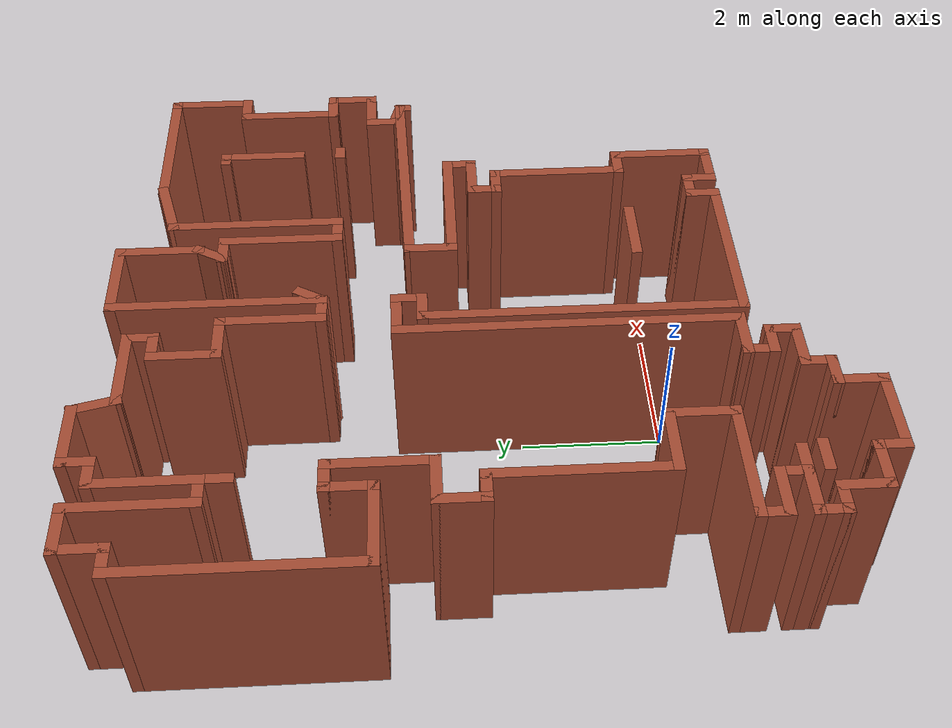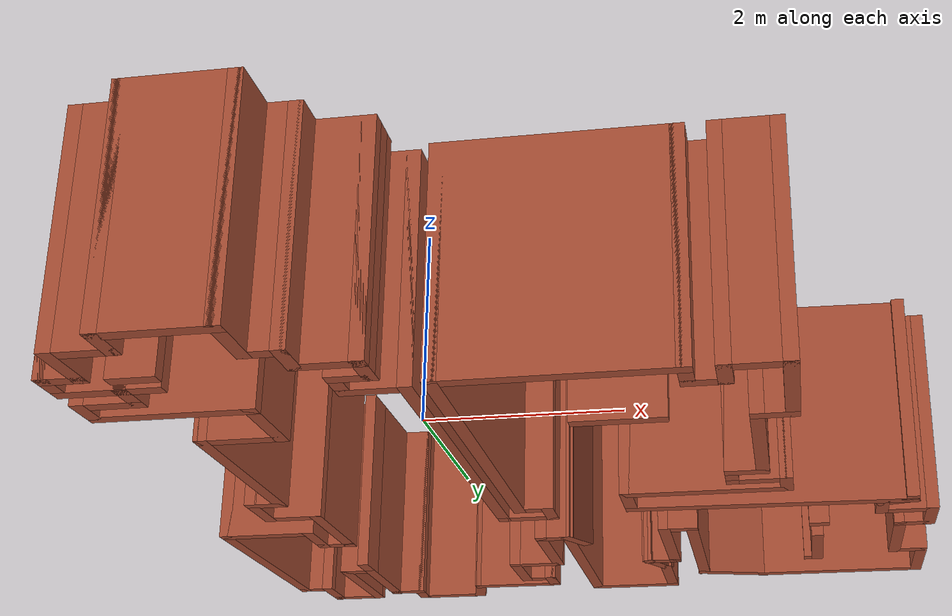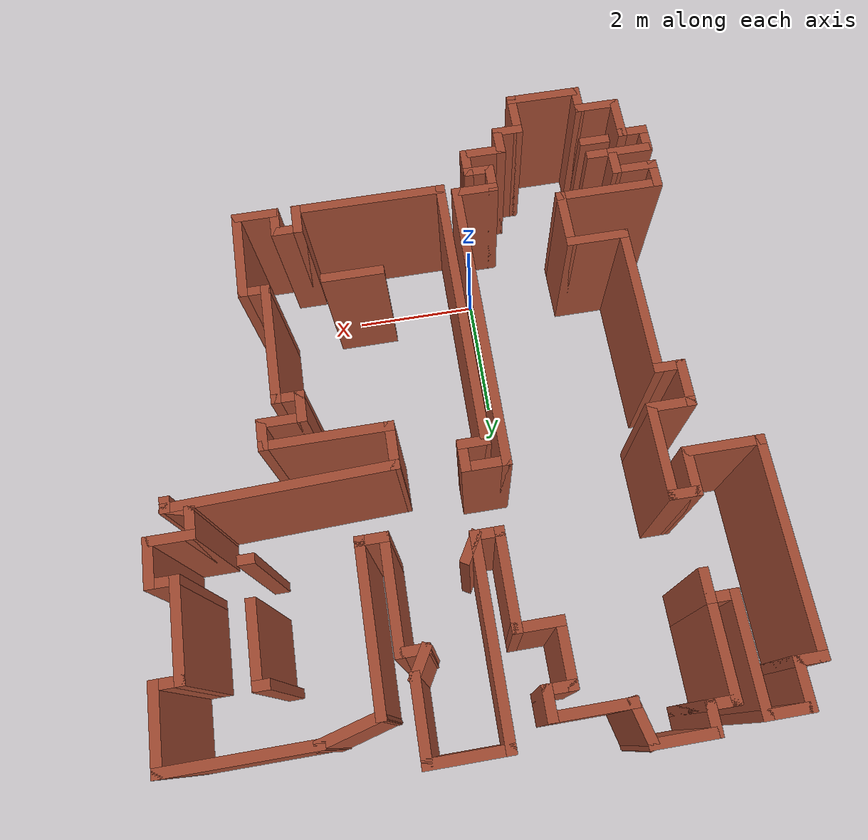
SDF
<?xml version='1.0'?>
<sdf version='1.6'>
  <model name='map_46'>
    <pose frame=''>0.793554 2.66189 0 0 -0 0</pose>
    <link name='Wall_0'>
      <collision name='Wall_0_Collision'>
        <geometry>
          <box>
            <size>1 0.15 2.5</size>
          </box>
        </geometry>
        <pose frame=''>0 0 1.25 0 -0 0</pose>
      </collision>
      <visual name='Wall_0_Visual'>
        <pose frame=''>0 0 1.25 0 -0 0</pose>
        <geometry>
          <box>
            <size>1 0.15 2.5</size>
          </box>
        </geometry>
        <material>
          <script>
            <uri>file://media/materials/scripts/gazebo.material</uri>
            <name>Gazebo/Bricks</name>
          </script>
          <ambient>1 1 1 1</ambient>
        </material>
        <meta>
          <layer>0</layer>
        </meta>
      </visual>
      <pose frame=''>-2.35596 5.16721 0 0 -0 3.14159</pose>
    </link>
    <link name='Wall_1'>
      <collision name='Wall_1_Collision'>
        <geometry>
          <box>
            <size>0.5 0.15 2.5</size>
          </box>
        </geometry>
        <pose frame=''>0 0 1.25 0 -0 0</pose>
      </collision>
      <visual name='Wall_1_Visual'>
        <pose frame=''>0 0 1.25 0 -0 0</pose>
        <geometry>
          <box>
            <size>0.5 0.15 2.5</size>
          </box>
        </geometry>
        <material>
          <script>
            <uri>file://media/materials/scripts/gazebo.material</uri>
            <name>Gazebo/Bricks</name>
          </script>
          <ambient>1 1 1 1</ambient>
        </material>
        <meta>
          <layer>0</layer>
        </meta>
      </visual>
      <pose frame=''>-2.78096 4.99221 0 0 -0 -1.5708</pose>
    </link>
    <link name='Wall_10'>
      <collision name='Wall_10_Collision'>
        <geometry>
          <box>
            <size>1.25 0.15 2.5</size>
          </box>
        </geometry>
        <pose frame=''>0 0 1.25 0 -0 0</pose>
      </collision>
      <visual name='Wall_10_Visual'>
        <pose frame=''>0 0 1.25 0 -0 0</pose>
        <geometry>
          <box>
            <size>1.25 0.15 2.5</size>
          </box>
        </geometry>
        <material>
          <script>
            <uri>file://media/materials/scripts/gazebo.material</uri>
            <name>Gazebo/Bricks</name>
          </script>
          <ambient>1 1 1 1</ambient>
        </material>
        <meta>
          <layer>0</layer>
        </meta>
      </visual>
      <pose frame=''>-3.88096 1.36721 0 0 -0 0</pose>
    </link>
    <link name='Wall_100'>
      <collision name='Wall_100_Collision'>
        <geometry>
          <box>
            <size>2.25 0.15 2.5</size>
          </box>
        </geometry>
        <pose frame=''>0 0 1.25 0 -0 0</pose>
      </collision>
      <visual name='Wall_100_Visual'>
        <pose frame=''>0 0 1.25 0 -0 0</pose>
        <geometry>
          <box>
            <size>2.25 0.15 2.5</size>
          </box>
        </geometry>
        <material>
          <script>
            <uri>file://media/materials/scripts/gazebo.material</uri>
            <name>Gazebo/Bricks</name>
          </script>
          <ambient>1 1 1 1</ambient>
        </material>
        <meta>
          <layer>0</layer>
        </meta>
      </visual>
      <pose frame=''>3.38096 4.45779 0 0 -0 3.14159</pose>
    </link>
    <link name='Wall_11'>
      <collision name='Wall_11_Collision'>
        <geometry>
          <box>
            <size>0.75 0.15 2.5</size>
          </box>
        </geometry>
        <pose frame=''>0 0 1.25 0 -0 0</pose>
      </collision>
      <visual name='Wall_11_Visual'>
        <pose frame=''>0 0 1.25 0 -0 0</pose>
        <geometry>
          <box>
            <size>0.75 0.15 2.5</size>
          </box>
        </geometry>
        <material>
          <script>
            <uri>file://media/materials/scripts/gazebo.material</uri>
            <name>Gazebo/Bricks</name>
          </script>
          <ambient>1 1 1 1</ambient>
        </material>
        <meta>
          <layer>0</layer>
        </meta>
      </visual>
      <pose frame=''>-3.33096 1.66721 0 0 -0 1.5708</pose>
    </link>
    <link name='Wall_112'>
      <collision name='Wall_112_Collision'>
        <geometry>
          <box>
            <size>1 0.15 2.5</size>
          </box>
        </geometry>
        <pose frame=''>0 0 1.25 0 -0 0</pose>
      </collision>
      <visual name='Wall_112_Visual'>
        <pose frame=''>0 0 1.25 0 -0 0</pose>
        <geometry>
          <box>
            <size>1 0.15 2.5</size>
          </box>
        </geometry>
        <material>
          <script>
            <uri>file://media/materials/scripts/gazebo.material</uri>
            <name>Gazebo/Bricks</name>
          </script>
          <ambient>1 1 1 1</ambient>
        </material>
        <meta>
          <layer>0</layer>
        </meta>
      </visual>
      <pose frame=''>1.92044 4.3478 0 0 -0 -2.87979</pose>
    </link>
    <link name='Wall_113'>
      <collision name='Wall_113_Collision'>
        <geometry>
          <box>
            <size>2.5 0.15 2.5</size>
          </box>
        </geometry>
        <pose frame=''>0 0 1.25 0 -0 0</pose>
      </collision>
      <visual name='Wall_113_Visual'>
        <pose frame=''>0 0 1.25 0 -0 0</pose>
        <geometry>
          <box>
            <size>2.5 0.15 2.5</size>
          </box>
        </geometry>
        <material>
          <script>
            <uri>file://media/materials/scripts/gazebo.material</uri>
            <name>Gazebo/Bricks</name>
          </script>
          <ambient>1 1 1 1</ambient>
        </material>
        <meta>
          <layer>0</layer>
        </meta>
      </visual>
      <pose frame=''>1.50993 3.0628 0 0 -0 -1.5708</pose>
    </link>
    <link name='Wall_114'>
      <collision name='Wall_114_Collision'>
        <geometry>
          <box>
            <size>0.5 0.15 2.5</size>
          </box>
        </geometry>
        <pose frame=''>0 0 1.25 0 -0 0</pose>
      </collision>
      <visual name='Wall_114_Visual'>
        <pose frame=''>0 0 1.25 0 -0 0</pose>
        <geometry>
          <box>
            <size>0.5 0.15 2.5</size>
          </box>
        </geometry>
        <material>
          <script>
            <uri>file://media/materials/scripts/gazebo.material</uri>
            <name>Gazebo/Bricks</name>
          </script>
          <ambient>1 1 1 1</ambient>
        </material>
        <meta>
          <layer>0</layer>
        </meta>
      </visual>
      <pose frame=''>1.33493 1.8878 0 0 -0 3.14159</pose>
    </link>
    <link name='Wall_115'>
      <collision name='Wall_115_Collision'>
        <geometry>
          <box>
            <size>1.75 0.15 2.5</size>
          </box>
        </geometry>
        <pose frame=''>0 0 1.25 0 -0 0</pose>
      </collision>
      <visual name='Wall_115_Visual'>
        <pose frame=''>0 0 1.25 0 -0 0</pose>
        <geometry>
          <box>
            <size>1.75 0.15 2.5</size>
          </box>
        </geometry>
        <material>
          <script>
            <uri>file://media/materials/scripts/gazebo.material</uri>
            <name>Gazebo/Bricks</name>
          </script>
          <ambient>1 1 1 1</ambient>
        </material>
        <meta>
          <layer>0</layer>
        </meta>
      </visual>
      <pose frame=''>1.15993 2.6878 0 0 -0 1.5708</pose>
    </link>
    <link name='Wall_119'>
      <collision name='Wall_119_Collision'>
        <geometry>
          <box>
            <size>1.25 0.15 2.5</size>
          </box>
        </geometry>
        <pose frame=''>0 0 1.25 0 -0 0</pose>
      </collision>
      <visual name='Wall_119_Visual'>
        <pose frame=''>0 0 1.25 0 -0 0</pose>
        <geometry>
          <box>
            <size>1.25 0.15 2.5</size>
          </box>
        </geometry>
        <material>
          <script>
            <uri>file://media/materials/scripts/gazebo.material</uri>
            <name>Gazebo/Bricks</name>
          </script>
          <ambient>1 1 1 1</ambient>
        </material>
        <meta>
          <layer>0</layer>
        </meta>
      </visual>
      <pose frame=''>1.00051 4.37587 0 0 -0 1.5708</pose>
    </link>
    <link name='Wall_12'>
      <collision name='Wall_12_Collision'>
        <geometry>
          <box>
            <size>0.5 0.15 2.5</size>
          </box>
        </geometry>
        <pose frame=''>0 0 1.25 0 -0 0</pose>
      </collision>
      <visual name='Wall_12_Visual'>
        <pose frame=''>0 0 1.25 0 -0 0</pose>
        <geometry>
          <box>
            <size>0.5 0.15 2.5</size>
          </box>
        </geometry>
        <material>
          <script>
            <uri>file://media/materials/scripts/gazebo.material</uri>
            <name>Gazebo/Bricks</name>
          </script>
          <ambient>1 1 1 1</ambient>
        </material>
        <meta>
          <layer>0</layer>
        </meta>
      </visual>
      <pose frame=''>-3.15596 1.96721 0 0 -0 0</pose>
    </link>
    <link name='Wall_122'>
      <collision name='Wall_122_Collision'>
        <geometry>
          <box>
            <size>1.25 0.15 2.5</size>
          </box>
        </geometry>
        <pose frame=''>0 0 1.25 0 -0 0</pose>
      </collision>
      <visual name='Wall_122_Visual'>
        <pose frame=''>0 0 1.25 0 -0 0</pose>
        <geometry>
          <box>
            <size>1.25 0.15 2.5</size>
          </box>
        </geometry>
        <material>
          <script>
            <uri>file://media/materials/scripts/gazebo.material</uri>
            <name>Gazebo/Bricks</name>
          </script>
          <ambient>1 1 1 1</ambient>
        </material>
        <meta>
          <layer>0</layer>
        </meta>
      </visual>
      <pose frame=''>0.450513 4.92587 0 0 -0 3.14159</pose>
    </link>
    <link name='Wall_123'>
      <collision name='Wall_123_Collision'>
        <geometry>
          <box>
            <size>3 0.15 2.5</size>
          </box>
        </geometry>
        <pose frame=''>0 0 1.25 0 -0 0</pose>
      </collision>
      <visual name='Wall_123_Visual'>
        <pose frame=''>0 0 1.25 0 -0 0</pose>
        <geometry>
          <box>
            <size>3 0.15 2.5</size>
          </box>
        </geometry>
        <material>
          <script>
            <uri>file://media/materials/scripts/gazebo.material</uri>
            <name>Gazebo/Bricks</name>
          </script>
          <ambient>1 1 1 1</ambient>
        </material>
        <meta>
          <layer>0</layer>
        </meta>
      </visual>
      <pose frame=''>-0.099487 3.50087 0 0 -0 -1.5708</pose>
    </link>
    <link name='Wall_124'>
      <collision name='Wall_124_Collision'>
        <geometry>
          <box>
            <size>0.5 0.15 2.5</size>
          </box>
        </geometry>
        <pose frame=''>0 0 1.25 0 -0 0</pose>
      </collision>
      <visual name='Wall_124_Visual'>
        <pose frame=''>0 0 1.25 0 -0 0</pose>
        <geometry>
          <box>
            <size>0.5 0.15 2.5</size>
          </box>
        </geometry>
        <material>
          <script>
            <uri>file://media/materials/scripts/gazebo.material</uri>
            <name>Gazebo/Bricks</name>
          </script>
          <ambient>1 1 1 1</ambient>
        </material>
        <meta>
          <layer>0</layer>
        </meta>
      </visual>
      <pose frame=''>-0.274487 2.07587 0 0 -0 3.14159</pose>
    </link>
    <link name='Wall_125'>
      <collision name='Wall_125_Collision'>
        <geometry>
          <box>
            <size>1.5 0.15 2.5</size>
          </box>
        </geometry>
        <pose frame=''>0 0 1.25 0 -0 0</pose>
      </collision>
      <visual name='Wall_125_Visual'>
        <pose frame=''>0 0 1.25 0 -0 0</pose>
        <geometry>
          <box>
            <size>1.5 0.15 2.5</size>
          </box>
        </geometry>
        <material>
          <script>
            <uri>file://media/materials/scripts/gazebo.material</uri>
            <name>Gazebo/Bricks</name>
          </script>
          <ambient>1 1 1 1</ambient>
        </material>
        <meta>
          <layer>0</layer>
        </meta>
      </visual>
      <pose frame=''>-0.449487 2.75087 0 0 -0 1.5708</pose>
    </link>
    <link name='Wall_126'>
      <collision name='Wall_126_Collision'>
        <geometry>
          <box>
            <size>0.75 0.15 2.5</size>
          </box>
        </geometry>
        <pose frame=''>0 0 1.25 0 -0 0</pose>
      </collision>
      <visual name='Wall_126_Visual'>
        <pose frame=''>0 0 1.25 0 -0 0</pose>
        <geometry>
          <box>
            <size>0.75 0.15 2.5</size>
          </box>
        </geometry>
        <material>
          <script>
            <uri>file://media/materials/scripts/gazebo.material</uri>
            <name>Gazebo/Bricks</name>
          </script>
          <ambient>1 1 1 1</ambient>
        </material>
        <meta>
          <layer>0</layer>
        </meta>
      </visual>
      <pose frame=''>-0.749487 3.42587 0 0 -0 3.14159</pose>
    </link>
    <link name='Wall_127'>
      <collision name='Wall_127_Collision'>
        <geometry>
          <box>
            <size>1 0.15 2.5</size>
          </box>
        </geometry>
        <pose frame=''>0 0 1.25 0 -0 0</pose>
      </collision>
      <visual name='Wall_127_Visual'>
        <pose frame=''>0 0 1.25 0 -0 0</pose>
        <geometry>
          <box>
            <size>1 0.15 2.5</size>
          </box>
        </geometry>
        <material>
          <script>
            <uri>file://media/materials/scripts/gazebo.material</uri>
            <name>Gazebo/Bricks</name>
          </script>
          <ambient>1 1 1 1</ambient>
        </material>
        <meta>
          <layer>0</layer>
        </meta>
      </visual>
      <pose frame=''>-1.04949 3.85087 0 0 -0 1.5708</pose>
    </link>
    <link name='Wall_128'>
      <collision name='Wall_128_Collision'>
        <geometry>
          <box>
            <size>0.5 0.15 2.5</size>
          </box>
        </geometry>
        <pose frame=''>0 0 1.25 0 -0 0</pose>
      </collision>
      <visual name='Wall_128_Visual'>
        <pose frame=''>0 0 1.25 0 -0 0</pose>
        <geometry>
          <box>
            <size>0.5 0.15 2.5</size>
          </box>
        </geometry>
        <material>
          <script>
            <uri>file://media/materials/scripts/gazebo.material</uri>
            <name>Gazebo/Bricks</name>
          </script>
          <ambient>1 1 1 1</ambient>
        </material>
        <meta>
          <layer>0</layer>
        </meta>
      </visual>
      <pose frame=''>-0.874487 4.27587 0 0 -0 0</pose>
    </link>
    <link name='Wall_129'>
      <collision name='Wall_129_Collision'>
        <geometry>
          <box>
            <size>0.5 0.15 2.5</size>
          </box>
        </geometry>
        <pose frame=''>0 0 1.25 0 -0 0</pose>
      </collision>
      <visual name='Wall_129_Visual'>
        <pose frame=''>0 0 1.25 0 -0 0</pose>
        <geometry>
          <box>
            <size>0.5 0.15 2.5</size>
          </box>
        </geometry>
        <material>
          <script>
            <uri>file://media/materials/scripts/gazebo.material</uri>
            <name>Gazebo/Bricks</name>
          </script>
          <ambient>1 1 1 1</ambient>
        </material>
        <meta>
          <layer>0</layer>
        </meta>
      </visual>
      <pose frame=''>-0.699487 4.45087 0 0 -0 1.5708</pose>
    </link>
    <link name='Wall_13'>
      <collision name='Wall_13_Collision'>
        <geometry>
          <box>
            <size>1.5 0.15 2.5</size>
          </box>
        </geometry>
        <pose frame=''>0 0 1.25 0 -0 0</pose>
      </collision>
      <visual name='Wall_13_Visual'>
        <pose frame=''>0 0 1.25 0 -0 0</pose>
        <geometry>
          <box>
            <size>1.5 0.15 2.5</size>
          </box>
        </geometry>
        <material>
          <script>
            <uri>file://media/materials/scripts/gazebo.material</uri>
            <name>Gazebo/Bricks</name>
          </script>
          <ambient>1 1 1 1</ambient>
        </material>
        <meta>
          <layer>0</layer>
        </meta>
      </visual>
      <pose frame=''>-2.98096 1.29221 0 0 -0 -1.5708</pose>
    </link>
    <link name='Wall_130'>
      <collision name='Wall_130_Collision'>
        <geometry>
          <box>
            <size>1.25 0.15 2.5</size>
          </box>
        </geometry>
        <pose frame=''>0 0 1.25 0 -0 0</pose>
      </collision>
      <visual name='Wall_130_Visual'>
        <pose frame=''>0 0 1.25 0 -0 0</pose>
        <geometry>
          <box>
            <size>1.25 0.15 2.5</size>
          </box>
        </geometry>
        <material>
          <script>
            <uri>file://media/materials/scripts/gazebo.material</uri>
            <name>Gazebo/Bricks</name>
          </script>
          <ambient>1 1 1 1</ambient>
        </material>
        <meta>
          <layer>0</layer>
        </meta>
      </visual>
      <pose frame=''>-1.24949 4.62587 0 0 -0 3.14159</pose>
    </link>
    <link name='Wall_131'>
      <collision name='Wall_131_Collision'>
        <geometry>
          <box>
            <size>0.707073 0.15 2.5</size>
          </box>
        </geometry>
        <pose frame=''>0 0 1.25 0 -0 0</pose>
      </collision>
      <visual name='Wall_131_Visual'>
        <pose frame=''>0 0 1.25 0 -0 0</pose>
        <geometry>
          <box>
            <size>0.707073 0.15 2.5</size>
          </box>
        </geometry>
        <material>
          <script>
            <uri>file://media/materials/scripts/gazebo.material</uri>
            <name>Gazebo/Bricks</name>
          </script>
          <ambient>1 1 1 1</ambient>
        </material>
        <meta>
          <layer>0</layer>
        </meta>
      </visual>
      <pose frame=''>-1.86522 4.89654 0 0 -0 1.80906</pose>
    </link>
    <link name='Wall_133'>
      <collision name='Wall_133_Collision'>
        <geometry>
          <box>
            <size>3.45152 0.15 2.5</size>
          </box>
        </geometry>
        <pose frame=''>0 0 1.25 0 -0 0</pose>
      </collision>
      <visual name='Wall_133_Visual'>
        <pose frame=''>0 0 1.25 0 -0 0</pose>
        <geometry>
          <box>
            <size>3.45152 0.15 2.5</size>
          </box>
        </geometry>
        <material>
          <script>
            <uri>file://media/materials/scripts/gazebo.material</uri>
            <name>Gazebo/Bricks</name>
          </script>
          <ambient>1 1 1 1</ambient>
        </material>
        <meta>
          <layer>0</layer>
        </meta>
      </visual>
      <pose frame=''>2.51904 0.917209 0 0 -0 0.030294</pose>
    </link>
    <link name='Wall_135'>
      <collision name='Wall_135_Collision'>
        <geometry>
          <box>
            <size>0.5 0.15 2.5</size>
          </box>
        </geometry>
        <pose frame=''>0 0 1.25 0 -0 0</pose>
      </collision>
      <visual name='Wall_135_Visual'>
        <pose frame=''>0 0 1.25 0 -0 0</pose>
        <geometry>
          <box>
            <size>0.5 0.15 2.5</size>
          </box>
        </geometry>
        <material>
          <script>
            <uri>file://media/materials/scripts/gazebo.material</uri>
            <name>Gazebo/Bricks</name>
          </script>
          <ambient>1 1 1 1</ambient>
        </material>
        <meta>
          <layer>0</layer>
        </meta>
      </visual>
      <pose frame=''>-0.011987 2.22743 0 0 -0 1.0472</pose>
    </link>
    <link name='Wall_137'>
      <collision name='Wall_137_Collision'>
        <geometry>
          <box>
            <size>0.25 0.15 2.5</size>
          </box>
        </geometry>
        <pose frame=''>0 0 1.25 0 -0 0</pose>
      </collision>
      <visual name='Wall_137_Visual'>
        <pose frame=''>0 0 1.25 0 -0 0</pose>
        <geometry>
          <box>
            <size>0.25 0.15 2.5</size>
          </box>
        </geometry>
        <material>
          <script>
            <uri>file://media/materials/scripts/gazebo.material</uri>
            <name>Gazebo/Bricks</name>
          </script>
          <ambient>1 1 1 1</ambient>
        </material>
        <meta>
          <layer>0</layer>
        </meta>
      </visual>
      <pose frame=''>3.02273 3.59433 0 0 -0 0</pose>
    </link>
    <link name='Wall_138'>
      <collision name='Wall_138_Collision'>
        <geometry>
          <box>
            <size>1.25 0.15 2.5</size>
          </box>
        </geometry>
        <pose frame=''>0 0 1.25 0 -0 0</pose>
      </collision>
      <visual name='Wall_138_Visual'>
        <pose frame=''>0 0 1.25 0 -0 0</pose>
        <geometry>
          <box>
            <size>1.25 0.15 2.5</size>
          </box>
        </geometry>
        <material>
          <script>
            <uri>file://media/materials/scripts/gazebo.material</uri>
            <name>Gazebo/Bricks</name>
          </script>
          <ambient>1 1 1 1</ambient>
        </material>
        <meta>
          <layer>0</layer>
        </meta>
      </visual>
      <pose frame=''>3.07273 3.04433 0 0 -0 -1.5708</pose>
    </link>
    <link name='Wall_14'>
      <collision name='Wall_14_Collision'>
        <geometry>
          <box>
            <size>0.75 0.15 2.5</size>
          </box>
        </geometry>
        <pose frame=''>0 0 1.25 0 -0 0</pose>
      </collision>
      <visual name='Wall_14_Visual'>
        <pose frame=''>0 0 1.25 0 -0 0</pose>
        <geometry>
          <box>
            <size>0.75 0.15 2.5</size>
          </box>
        </geometry>
        <material>
          <script>
            <uri>file://media/materials/scripts/gazebo.material</uri>
            <name>Gazebo/Bricks</name>
          </script>
          <ambient>1 1 1 1</ambient>
        </material>
        <meta>
          <layer>0</layer>
        </meta>
      </visual>
      <pose frame=''>-3.28096 0.617209 0 0 -0 3.14159</pose>
    </link>
    <link name='Wall_140'>
      <collision name='Wall_140_Collision'>
        <geometry>
          <box>
            <size>0.25 0.15 2.5</size>
          </box>
        </geometry>
        <pose frame=''>0 0 1.25 0 -0 0</pose>
      </collision>
      <visual name='Wall_140_Visual'>
        <pose frame=''>0 0 1.25 0 -0 0</pose>
        <geometry>
          <box>
            <size>0.25 0.15 2.5</size>
          </box>
        </geometry>
        <material>
          <script>
            <uri>file://media/materials/scripts/gazebo.material</uri>
            <name>Gazebo/Bricks</name>
          </script>
          <ambient>1 1 1 1</ambient>
        </material>
        <meta>
          <layer>0</layer>
        </meta>
      </visual>
      <pose frame=''>3.09212 1.88266 0 0 -0 0</pose>
    </link>
    <link name='Wall_144'>
      <collision name='Wall_144_Collision'>
        <geometry>
          <box>
            <size>0.5 0.15 2.5</size>
          </box>
        </geometry>
        <pose frame=''>0 0 1.25 0 -0 0</pose>
      </collision>
      <visual name='Wall_144_Visual'>
        <pose frame=''>0 0 1.25 0 -0 0</pose>
        <geometry>
          <box>
            <size>0.5 0.15 2.5</size>
          </box>
        </geometry>
        <material>
          <script>
            <uri>file://media/materials/scripts/gazebo.material</uri>
            <name>Gazebo/Bricks</name>
          </script>
          <ambient>1 1 1 1</ambient>
        </material>
        <meta>
          <layer>0</layer>
        </meta>
      </visual>
      <pose frame=''>-3.13096 3.29221 0 0 -0 -1.5708</pose>
    </link>
    <link name='Wall_146'>
      <collision name='Wall_146_Collision'>
        <geometry>
          <box>
            <size>1 0.15 2.5</size>
          </box>
        </geometry>
        <pose frame=''>0 0 1.25 0 -0 0</pose>
      </collision>
      <visual name='Wall_146_Visual'>
        <pose frame=''>0 0 1.25 0 -0 0</pose>
        <geometry>
          <box>
            <size>1 0.15 2.5</size>
          </box>
        </geometry>
        <material>
          <script>
            <uri>file://media/materials/scripts/gazebo.material</uri>
            <name>Gazebo/Bricks</name>
          </script>
          <ambient>1 1 1 1</ambient>
        </material>
        <meta>
          <layer>0</layer>
        </meta>
      </visual>
      <pose frame=''>1.1078 -2.32711 0 0 -0 0</pose>
    </link>
    <link name='Wall_148'>
      <collision name='Wall_148_Collision'>
        <geometry>
          <box>
            <size>0.5 0.15 2.5</size>
          </box>
        </geometry>
        <pose frame=''>0 0 1.25 0 -0 0</pose>
      </collision>
      <visual name='Wall_148_Visual'>
        <pose frame=''>0 0 1.25 0 -0 0</pose>
        <geometry>
          <box>
            <size>0.5 0.15 2.5</size>
          </box>
        </geometry>
        <material>
          <script>
            <uri>file://media/materials/scripts/gazebo.material</uri>
            <name>Gazebo/Bricks</name>
          </script>
          <ambient>1 1 1 1</ambient>
        </material>
        <meta>
          <layer>0</layer>
        </meta>
      </visual>
      <pose frame=''>-3.20596 -3.88279 0 0 -0 0</pose>
    </link>
    <link name='Wall_15'>
      <collision name='Wall_15_Collision'>
        <geometry>
          <box>
            <size>0.75 0.15 2.5</size>
          </box>
        </geometry>
        <pose frame=''>0 0 1.25 0 -0 0</pose>
      </collision>
      <visual name='Wall_15_Visual'>
        <pose frame=''>0 0 1.25 0 -0 0</pose>
        <geometry>
          <box>
            <size>0.75 0.15 2.5</size>
          </box>
        </geometry>
        <material>
          <script>
            <uri>file://media/materials/scripts/gazebo.material</uri>
            <name>Gazebo/Bricks</name>
          </script>
          <ambient>1 1 1 1</ambient>
        </material>
        <meta>
          <layer>0</layer>
        </meta>
      </visual>
      <pose frame=''>-3.58096 0.317209 0 0 -0 -1.5708</pose>
    </link>
    <link name='Wall_150'>
      <collision name='Wall_150_Collision'>
        <geometry>
          <box>
            <size>0.5 0.15 2.5</size>
          </box>
        </geometry>
        <pose frame=''>0 0 1.25 0 -0 0</pose>
      </collision>
      <visual name='Wall_150_Visual'>
        <pose frame=''>0 0 1.25 0 -0 0</pose>
        <geometry>
          <box>
            <size>0.5 0.15 2.5</size>
          </box>
        </geometry>
        <material>
          <script>
            <uri>file://media/materials/scripts/gazebo.material</uri>
            <name>Gazebo/Bricks</name>
          </script>
          <ambient>1 1 1 1</ambient>
        </material>
        <meta>
          <layer>0</layer>
        </meta>
      </visual>
      <pose frame=''>-3.1438 -4.15443 0 0 -0 0</pose>
    </link>
    <link name='Wall_153'>
      <collision name='Wall_153_Collision'>
        <geometry>
          <box>
            <size>0.5 0.15 2.5</size>
          </box>
        </geometry>
        <pose frame=''>0 0 1.25 0 -0 0</pose>
      </collision>
      <visual name='Wall_153_Visual'>
        <pose frame=''>0 0 1.25 0 -0 0</pose>
        <geometry>
          <box>
            <size>0.5 0.15 2.5</size>
          </box>
        </geometry>
        <material>
          <script>
            <uri>file://media/materials/scripts/gazebo.material</uri>
            <name>Gazebo/Bricks</name>
          </script>
          <ambient>1 1 1 1</ambient>
        </material>
        <meta>
          <layer>0</layer>
        </meta>
      </visual>
      <pose frame=''>0.984926 3.4878 0 0 -0 3.14159</pose>
    </link>
    <link name='Wall_154'>
      <collision name='Wall_154_Collision'>
        <geometry>
          <box>
            <size>0.538094 0.15 2.5</size>
          </box>
        </geometry>
        <pose frame=''>0 0 1.25 0 -0 0</pose>
      </collision>
      <visual name='Wall_154_Visual'>
        <pose frame=''>0 0 1.25 0 -0 0</pose>
        <geometry>
          <box>
            <size>0.538094 0.15 2.5</size>
          </box>
        </geometry>
        <material>
          <script>
            <uri>file://media/materials/scripts/gazebo.material</uri>
            <name>Gazebo/Bricks</name>
          </script>
          <ambient>1 1 1 1</ambient>
        </material>
        <meta>
          <layer>0</layer>
        </meta>
      </visual>
      <pose frame=''>0.905219 3.65684 0 0 -0 1.05746</pose>
    </link>
    <link name='Wall_16'>
      <collision name='Wall_16_Collision'>
        <geometry>
          <box>
            <size>0.5 0.15 2.5</size>
          </box>
        </geometry>
        <pose frame=''>0 0 1.25 0 -0 0</pose>
      </collision>
      <visual name='Wall_16_Visual'>
        <pose frame=''>0 0 1.25 0 -0 0</pose>
        <geometry>
          <box>
            <size>0.5 0.15 2.5</size>
          </box>
        </geometry>
        <material>
          <script>
            <uri>file://media/materials/scripts/gazebo.material</uri>
            <name>Gazebo/Bricks</name>
          </script>
          <ambient>1 1 1 1</ambient>
        </material>
        <meta>
          <layer>0</layer>
        </meta>
      </visual>
      <pose frame=''>-3.40596 0.017209 0 0 -0 0</pose>
    </link>
    <link name='Wall_17'>
      <collision name='Wall_17_Collision'>
        <geometry>
          <box>
            <size>2.5 0.15 2.5</size>
          </box>
        </geometry>
        <pose frame=''>0 0 1.25 0 -0 0</pose>
      </collision>
      <visual name='Wall_17_Visual'>
        <pose frame=''>0 0 1.25 0 -0 0</pose>
        <geometry>
          <box>
            <size>2.5 0.15 2.5</size>
          </box>
        </geometry>
        <material>
          <script>
            <uri>file://media/materials/scripts/gazebo.material</uri>
            <name>Gazebo/Bricks</name>
          </script>
          <ambient>1 1 1 1</ambient>
        </material>
        <meta>
          <layer>0</layer>
        </meta>
      </visual>
      <pose frame=''>-3.23096 -1.15779 0 0 -0 -1.5708</pose>
    </link>
    <link name='Wall_18'>
      <collision name='Wall_18_Collision'>
        <geometry>
          <box>
            <size>1 0.15 2.5</size>
          </box>
        </geometry>
        <pose frame=''>0 0 1.25 0 -0 0</pose>
      </collision>
      <visual name='Wall_18_Visual'>
        <pose frame=''>0 0 1.25 0 -0 0</pose>
        <geometry>
          <box>
            <size>1 0.15 2.5</size>
          </box>
        </geometry>
        <material>
          <script>
            <uri>file://media/materials/scripts/gazebo.material</uri>
            <name>Gazebo/Bricks</name>
          </script>
          <ambient>1 1 1 1</ambient>
        </material>
        <meta>
          <layer>0</layer>
        </meta>
      </visual>
      <pose frame=''>-2.80596 -2.33279 0 0 -0 0</pose>
    </link>
    <link name='Wall_19'>
      <collision name='Wall_19_Collision'>
        <geometry>
          <box>
            <size>1 0.15 2.5</size>
          </box>
        </geometry>
        <pose frame=''>0 0 1.25 0 -0 0</pose>
      </collision>
      <visual name='Wall_19_Visual'>
        <pose frame=''>0 0 1.25 0 -0 0</pose>
        <geometry>
          <box>
            <size>1 0.15 2.5</size>
          </box>
        </geometry>
        <material>
          <script>
            <uri>file://media/materials/scripts/gazebo.material</uri>
            <name>Gazebo/Bricks</name>
          </script>
          <ambient>1 1 1 1</ambient>
        </material>
        <meta>
          <layer>0</layer>
        </meta>
      </visual>
      <pose frame=''>-2.38096 -2.75779 0 0 -0 -1.5708</pose>
    </link>
    <link name='Wall_2'>
      <collision name='Wall_2_Collision'>
        <geometry>
          <box>
            <size>0.5 0.15 2.5</size>
          </box>
        </geometry>
        <pose frame=''>0 0 1.25 0 -0 0</pose>
      </collision>
      <visual name='Wall_2_Visual'>
        <pose frame=''>0 0 1.25 0 -0 0</pose>
        <geometry>
          <box>
            <size>0.5 0.15 2.5</size>
          </box>
        </geometry>
        <material>
          <script>
            <uri>file://media/materials/scripts/gazebo.material</uri>
            <name>Gazebo/Bricks</name>
          </script>
          <ambient>1 1 1 1</ambient>
        </material>
        <meta>
          <layer>0</layer>
        </meta>
      </visual>
      <pose frame=''>-2.95596 4.81721 0 0 -0 3.14159</pose>
    </link>
    <link name='Wall_20'>
      <collision name='Wall_20_Collision'>
        <geometry>
          <box>
            <size>1.75 0.15 2.5</size>
          </box>
        </geometry>
        <pose frame=''>0 0 1.25 0 -0 0</pose>
      </collision>
      <visual name='Wall_20_Visual'>
        <pose frame=''>0 0 1.25 0 -0 0</pose>
        <geometry>
          <box>
            <size>1.75 0.15 2.5</size>
          </box>
        </geometry>
        <material>
          <script>
            <uri>file://media/materials/scripts/gazebo.material</uri>
            <name>Gazebo/Bricks</name>
          </script>
          <ambient>1 1 1 1</ambient>
        </material>
        <meta>
          <layer>0</layer>
        </meta>
      </visual>
      <pose frame=''>-3.18096 -3.18279 0 0 -0 3.14159</pose>
    </link>
    <link name='Wall_21'>
      <collision name='Wall_21_Collision'>
        <geometry>
          <box>
            <size>0.5 0.15 2.5</size>
          </box>
        </geometry>
        <pose frame=''>0 0 1.25 0 -0 0</pose>
      </collision>
      <visual name='Wall_21_Visual'>
        <pose frame=''>0 0 1.25 0 -0 0</pose>
        <geometry>
          <box>
            <size>0.5 0.15 2.5</size>
          </box>
        </geometry>
        <material>
          <script>
            <uri>file://media/materials/scripts/gazebo.material</uri>
            <name>Gazebo/Bricks</name>
          </script>
          <ambient>1 1 1 1</ambient>
        </material>
        <meta>
          <layer>0</layer>
        </meta>
      </visual>
      <pose frame=''>-3.98096 -3.35779 0 0 -0 -1.5708</pose>
    </link>
    <link name='Wall_22'>
      <collision name='Wall_22_Collision'>
        <geometry>
          <box>
            <size>0.75 0.15 2.5</size>
          </box>
        </geometry>
        <pose frame=''>0 0 1.25 0 -0 0</pose>
      </collision>
      <visual name='Wall_22_Visual'>
        <pose frame=''>0 0 1.25 0 -0 0</pose>
        <geometry>
          <box>
            <size>0.75 0.15 2.5</size>
          </box>
        </geometry>
        <material>
          <script>
            <uri>file://media/materials/scripts/gazebo.material</uri>
            <name>Gazebo/Bricks</name>
          </script>
          <ambient>1 1 1 1</ambient>
        </material>
        <meta>
          <layer>0</layer>
        </meta>
      </visual>
      <pose frame=''>-3.68096 -3.53279 0 0 -0 0</pose>
    </link>
    <link name='Wall_23'>
      <collision name='Wall_23_Collision'>
        <geometry>
          <box>
            <size>0.5 0.15 2.5</size>
          </box>
        </geometry>
        <pose frame=''>0 0 1.25 0 -0 0</pose>
      </collision>
      <visual name='Wall_23_Visual'>
        <pose frame=''>0 0 1.25 0 -0 0</pose>
        <geometry>
          <box>
            <size>0.5 0.15 2.5</size>
          </box>
        </geometry>
        <material>
          <script>
            <uri>file://media/materials/scripts/gazebo.material</uri>
            <name>Gazebo/Bricks</name>
          </script>
          <ambient>1 1 1 1</ambient>
        </material>
        <meta>
          <layer>0</layer>
        </meta>
      </visual>
      <pose frame=''>-3.38096 -3.70779 0 0 -0 -1.5708</pose>
    </link>
    <link name='Wall_24'>
      <collision name='Wall_24_Collision'>
        <geometry>
          <box>
            <size>0.75 0.15 2.5</size>
          </box>
        </geometry>
        <pose frame=''>0 0 1.25 0 -0 0</pose>
      </collision>
      <visual name='Wall_24_Visual'>
        <pose frame=''>0 0 1.25 0 -0 0</pose>
        <geometry>
          <box>
            <size>0.75 0.15 2.5</size>
          </box>
        </geometry>
        <material>
          <script>
            <uri>file://media/materials/scripts/gazebo.material</uri>
            <name>Gazebo/Bricks</name>
          </script>
          <ambient>1 1 1 1</ambient>
        </material>
        <meta>
          <layer>0</layer>
        </meta>
      </visual>
      <pose frame=''>-3.68096 -3.88279 0 0 -0 3.14159</pose>
    </link>
    <link name='Wall_28'>
      <collision name='Wall_28_Collision'>
        <geometry>
          <box>
            <size>0.5 0.15 2.5</size>
          </box>
        </geometry>
        <pose frame=''>0 0 1.25 0 -0 0</pose>
      </collision>
      <visual name='Wall_28_Visual'>
        <pose frame=''>0 0 1.25 0 -0 0</pose>
        <geometry>
          <box>
            <size>0.5 0.15 2.5</size>
          </box>
        </geometry>
        <material>
          <script>
            <uri>file://media/materials/scripts/gazebo.material</uri>
            <name>Gazebo/Bricks</name>
          </script>
          <ambient>1 1 1 1</ambient>
        </material>
        <meta>
          <layer>0</layer>
        </meta>
      </visual>
      <pose frame=''>-3.98096 -4.05779 0 0 -0 -1.5708</pose>
    </link>
    <link name='Wall_29'>
      <collision name='Wall_29_Collision'>
        <geometry>
          <box>
            <size>0.5 0.15 2.5</size>
          </box>
        </geometry>
        <pose frame=''>0 0 1.25 0 -0 0</pose>
      </collision>
      <visual name='Wall_29_Visual'>
        <pose frame=''>0 0 1.25 0 -0 0</pose>
        <geometry>
          <box>
            <size>0.5 0.15 2.5</size>
          </box>
        </geometry>
        <material>
          <script>
            <uri>file://media/materials/scripts/gazebo.material</uri>
            <name>Gazebo/Bricks</name>
          </script>
          <ambient>1 1 1 1</ambient>
        </material>
        <meta>
          <layer>0</layer>
        </meta>
      </visual>
      <pose frame=''>-3.80596 -4.23279 0 0 -0 0</pose>
    </link>
    <link name='Wall_3'>
      <collision name='Wall_3_Collision'>
        <geometry>
          <box>
            <size>1.5 0.15 2.5</size>
          </box>
        </geometry>
        <pose frame=''>0 0 1.25 0 -0 0</pose>
      </collision>
      <visual name='Wall_3_Visual'>
        <pose frame=''>0 0 1.25 0 -0 0</pose>
        <geometry>
          <box>
            <size>1.5 0.15 2.5</size>
          </box>
        </geometry>
        <material>
          <script>
            <uri>file://media/materials/scripts/gazebo.material</uri>
            <name>Gazebo/Bricks</name>
          </script>
          <ambient>1 1 1 1</ambient>
        </material>
        <meta>
          <layer>0</layer>
        </meta>
      </visual>
      <pose frame=''>-3.13096 4.14221 0 0 -0 -1.5708</pose>
    </link>
    <link name='Wall_30'>
      <collision name='Wall_30_Collision'>
        <geometry>
          <box>
            <size>0.75 0.15 2.5</size>
          </box>
        </geometry>
        <pose frame=''>0 0 1.25 0 -0 0</pose>
      </collision>
      <visual name='Wall_30_Visual'>
        <pose frame=''>0 0 1.25 0 -0 0</pose>
        <geometry>
          <box>
            <size>0.75 0.15 2.5</size>
          </box>
        </geometry>
        <material>
          <script>
            <uri>file://media/materials/scripts/gazebo.material</uri>
            <name>Gazebo/Bricks</name>
          </script>
          <ambient>1 1 1 1</ambient>
        </material>
        <meta>
          <layer>0</layer>
        </meta>
      </visual>
      <pose frame=''>-3.63096 -4.53279 0 0 -0 -1.5708</pose>
    </link>
    <link name='Wall_31'>
      <collision name='Wall_31_Collision'>
        <geometry>
          <box>
            <size>0.75 0.15 2.5</size>
          </box>
        </geometry>
        <pose frame=''>0 0 1.25 0 -0 0</pose>
      </collision>
      <visual name='Wall_31_Visual'>
        <pose frame=''>0 0 1.25 0 -0 0</pose>
        <geometry>
          <box>
            <size>0.75 0.15 2.5</size>
          </box>
        </geometry>
        <material>
          <script>
            <uri>file://media/materials/scripts/gazebo.material</uri>
            <name>Gazebo/Bricks</name>
          </script>
          <ambient>1 1 1 1</ambient>
        </material>
        <meta>
          <layer>0</layer>
        </meta>
      </visual>
      <pose frame=''>-3.33096 -4.83279 0 0 -0 0</pose>
    </link>
    <link name='Wall_32'>
      <collision name='Wall_32_Collision'>
        <geometry>
          <box>
            <size>0.5 0.15 2.5</size>
          </box>
        </geometry>
        <pose frame=''>0 0 1.25 0 -0 0</pose>
      </collision>
      <visual name='Wall_32_Visual'>
        <pose frame=''>0 0 1.25 0 -0 0</pose>
        <geometry>
          <box>
            <size>0.5 0.15 2.5</size>
          </box>
        </geometry>
        <material>
          <script>
            <uri>file://media/materials/scripts/gazebo.material</uri>
            <name>Gazebo/Bricks</name>
          </script>
          <ambient>1 1 1 1</ambient>
        </material>
        <meta>
          <layer>0</layer>
        </meta>
      </visual>
      <pose frame=''>-3.03096 -5.00779 0 0 -0 -1.5708</pose>
    </link>
    <link name='Wall_37'>
      <collision name='Wall_37_Collision'>
        <geometry>
          <box>
            <size>1.25 0.15 2.5</size>
          </box>
        </geometry>
        <pose frame=''>0 0 1.25 0 -0 0</pose>
      </collision>
      <visual name='Wall_37_Visual'>
        <pose frame=''>0 0 1.25 0 -0 0</pose>
        <geometry>
          <box>
            <size>1.25 0.15 2.5</size>
          </box>
        </geometry>
        <material>
          <script>
            <uri>file://media/materials/scripts/gazebo.material</uri>
            <name>Gazebo/Bricks</name>
          </script>
          <ambient>1 1 1 1</ambient>
        </material>
        <meta>
          <layer>0</layer>
        </meta>
      </visual>
      <pose frame=''>-2.48096 -5.18279 0 0 -0 0</pose>
    </link>
    <link name='Wall_4'>
      <collision name='Wall_4_Collision'>
        <geometry>
          <box>
            <size>0.5 0.15 2.5</size>
          </box>
        </geometry>
        <pose frame=''>0 0 1.25 0 -0 0</pose>
      </collision>
      <visual name='Wall_4_Visual'>
        <pose frame=''>0 0 1.25 0 -0 0</pose>
        <geometry>
          <box>
            <size>0.5 0.15 2.5</size>
          </box>
        </geometry>
        <material>
          <script>
            <uri>file://media/materials/scripts/gazebo.material</uri>
            <name>Gazebo/Bricks</name>
          </script>
          <ambient>1 1 1 1</ambient>
        </material>
        <meta>
          <layer>0</layer>
        </meta>
      </visual>
      <pose frame=''>-3.30596 3.46721 0 0 -0 3.14159</pose>
    </link>
    <link name='Wall_40'>
      <collision name='Wall_40_Collision'>
        <geometry>
          <box>
            <size>0.75 0.15 2.5</size>
          </box>
        </geometry>
        <pose frame=''>0 0 1.25 0 -0 0</pose>
      </collision>
      <visual name='Wall_40_Visual'>
        <pose frame=''>0 0 1.25 0 -0 0</pose>
        <geometry>
          <box>
            <size>0.75 0.15 2.5</size>
          </box>
        </geometry>
        <material>
          <script>
            <uri>file://media/materials/scripts/gazebo.material</uri>
            <name>Gazebo/Bricks</name>
          </script>
          <ambient>1 1 1 1</ambient>
        </material>
        <meta>
          <layer>0</layer>
        </meta>
      </visual>
      <pose frame=''>-1.93096 -4.88279 0 0 -0 1.5708</pose>
    </link>
    <link name='Wall_41'>
      <collision name='Wall_41_Collision'>
        <geometry>
          <box>
            <size>0.5 0.15 2.5</size>
          </box>
        </geometry>
        <pose frame=''>0 0 1.25 0 -0 0</pose>
      </collision>
      <visual name='Wall_41_Visual'>
        <pose frame=''>0 0 1.25 0 -0 0</pose>
        <geometry>
          <box>
            <size>0.5 0.15 2.5</size>
          </box>
        </geometry>
        <material>
          <script>
            <uri>file://media/materials/scripts/gazebo.material</uri>
            <name>Gazebo/Bricks</name>
          </script>
          <ambient>1 1 1 1</ambient>
        </material>
        <meta>
          <layer>0</layer>
        </meta>
      </visual>
      <pose frame=''>-1.75596 -4.58279 0 0 -0 0</pose>
    </link>
    <link name='Wall_42'>
      <collision name='Wall_42_Collision'>
        <geometry>
          <box>
            <size>0.5 0.15 2.5</size>
          </box>
        </geometry>
        <pose frame=''>0 0 1.25 0 -0 0</pose>
      </collision>
      <visual name='Wall_42_Visual'>
        <pose frame=''>0 0 1.25 0 -0 0</pose>
        <geometry>
          <box>
            <size>0.5 0.15 2.5</size>
          </box>
        </geometry>
        <material>
          <script>
            <uri>file://media/materials/scripts/gazebo.material</uri>
            <name>Gazebo/Bricks</name>
          </script>
          <ambient>1 1 1 1</ambient>
        </material>
        <meta>
          <layer>0</layer>
        </meta>
      </visual>
      <pose frame=''>-1.58096 -4.40779 0 0 -0 1.5708</pose>
    </link>
    <link name='Wall_45'>
      <collision name='Wall_45_Collision'>
        <geometry>
          <box>
            <size>0.75 0.15 2.5</size>
          </box>
        </geometry>
        <pose frame=''>0 0 1.25 0 -0 0</pose>
      </collision>
      <visual name='Wall_45_Visual'>
        <pose frame=''>0 0 1.25 0 -0 0</pose>
        <geometry>
          <box>
            <size>0.75 0.15 2.5</size>
          </box>
        </geometry>
        <material>
          <script>
            <uri>file://media/materials/scripts/gazebo.material</uri>
            <name>Gazebo/Bricks</name>
          </script>
          <ambient>1 1 1 1</ambient>
        </material>
        <meta>
          <layer>0</layer>
        </meta>
      </visual>
      <pose frame=''>-1.28096 -4.23279 0 0 -0 0</pose>
    </link>
    <link name='Wall_46'>
      <collision name='Wall_46_Collision'>
        <geometry>
          <box>
            <size>0.5 0.15 2.5</size>
          </box>
        </geometry>
        <pose frame=''>0 0 1.25 0 -0 0</pose>
      </collision>
      <visual name='Wall_46_Visual'>
        <pose frame=''>0 0 1.25 0 -0 0</pose>
        <geometry>
          <box>
            <size>0.5 0.15 2.5</size>
          </box>
        </geometry>
        <material>
          <script>
            <uri>file://media/materials/scripts/gazebo.material</uri>
            <name>Gazebo/Bricks</name>
          </script>
          <ambient>1 1 1 1</ambient>
        </material>
        <meta>
          <layer>0</layer>
        </meta>
      </visual>
      <pose frame=''>-0.980963 -4.05779 0 0 -0 1.5708</pose>
    </link>
    <link name='Wall_47'>
      <collision name='Wall_47_Collision'>
        <geometry>
          <box>
            <size>0.5 0.15 2.5</size>
          </box>
        </geometry>
        <pose frame=''>0 0 1.25 0 -0 0</pose>
      </collision>
      <visual name='Wall_47_Visual'>
        <pose frame=''>0 0 1.25 0 -0 0</pose>
        <geometry>
          <box>
            <size>0.5 0.15 2.5</size>
          </box>
        </geometry>
        <material>
          <script>
            <uri>file://media/materials/scripts/gazebo.material</uri>
            <name>Gazebo/Bricks</name>
          </script>
          <ambient>1 1 1 1</ambient>
        </material>
        <meta>
          <layer>0</layer>
        </meta>
      </visual>
      <pose frame=''>-1.15596 -3.88279 0 0 -0 3.14159</pose>
    </link>
    <link name='Wall_48'>
      <collision name='Wall_48_Collision'>
        <geometry>
          <box>
            <size>0.5 0.15 2.5</size>
          </box>
        </geometry>
        <pose frame=''>0 0 1.25 0 -0 0</pose>
      </collision>
      <visual name='Wall_48_Visual'>
        <pose frame=''>0 0 1.25 0 -0 0</pose>
        <geometry>
          <box>
            <size>0.5 0.15 2.5</size>
          </box>
        </geometry>
        <material>
          <script>
            <uri>file://media/materials/scripts/gazebo.material</uri>
            <name>Gazebo/Bricks</name>
          </script>
          <ambient>1 1 1 1</ambient>
        </material>
        <meta>
          <layer>0</layer>
        </meta>
      </visual>
      <pose frame=''>-1.33096 -3.70779 0 0 -0 1.5708</pose>
    </link>
    <link name='Wall_5'>
      <collision name='Wall_5_Collision'>
        <geometry>
          <box>
            <size>1.75 0.15 2.5</size>
          </box>
        </geometry>
        <pose frame=''>0 0 1.25 0 -0 0</pose>
      </collision>
      <visual name='Wall_5_Visual'>
        <pose frame=''>0 0 1.25 0 -0 0</pose>
        <geometry>
          <box>
            <size>1.75 0.15 2.5</size>
          </box>
        </geometry>
        <material>
          <script>
            <uri>file://media/materials/scripts/gazebo.material</uri>
            <name>Gazebo/Bricks</name>
          </script>
          <ambient>1 1 1 1</ambient>
        </material>
        <meta>
          <layer>0</layer>
        </meta>
      </visual>
      <pose frame=''>-3.48096 4.26721 0 0 -0 1.5708</pose>
    </link>
    <link name='Wall_51'>
      <collision name='Wall_51_Collision'>
        <geometry>
          <box>
            <size>0.75 0.15 2.5</size>
          </box>
        </geometry>
        <pose frame=''>0 0 1.25 0 -0 0</pose>
      </collision>
      <visual name='Wall_51_Visual'>
        <pose frame=''>0 0 1.25 0 -0 0</pose>
        <geometry>
          <box>
            <size>0.75 0.15 2.5</size>
          </box>
        </geometry>
        <material>
          <script>
            <uri>file://media/materials/scripts/gazebo.material</uri>
            <name>Gazebo/Bricks</name>
          </script>
          <ambient>1 1 1 1</ambient>
        </material>
        <meta>
          <layer>0</layer>
        </meta>
      </visual>
      <pose frame=''>-1.03096 -3.53279 0 0 -0 0</pose>
    </link>
    <link name='Wall_52'>
      <collision name='Wall_52_Collision'>
        <geometry>
          <box>
            <size>4.75 0.15 2.5</size>
          </box>
        </geometry>
        <pose frame=''>0 0 1.25 0 -0 0</pose>
      </collision>
      <visual name='Wall_52_Visual'>
        <pose frame=''>0 0 1.25 0 -0 0</pose>
        <geometry>
          <box>
            <size>4.75 0.15 2.5</size>
          </box>
        </geometry>
        <material>
          <script>
            <uri>file://media/materials/scripts/gazebo.material</uri>
            <name>Gazebo/Bricks</name>
          </script>
          <ambient>1 1 1 1</ambient>
        </material>
        <meta>
          <layer>0</layer>
        </meta>
      </visual>
      <pose frame=''>-0.730963 -1.23279 0 0 -0 1.5708</pose>
    </link>
    <link name='Wall_53'>
      <collision name='Wall_53_Collision'>
        <geometry>
          <box>
            <size>0.75 0.15 2.5</size>
          </box>
        </geometry>
        <pose frame=''>0 0 1.25 0 -0 0</pose>
      </collision>
      <visual name='Wall_53_Visual'>
        <pose frame=''>0 0 1.25 0 -0 0</pose>
        <geometry>
          <box>
            <size>0.75 0.15 2.5</size>
          </box>
        </geometry>
        <material>
          <script>
            <uri>file://media/materials/scripts/gazebo.material</uri>
            <name>Gazebo/Bricks</name>
          </script>
          <ambient>1 1 1 1</ambient>
        </material>
        <meta>
          <layer>0</layer>
        </meta>
      </visual>
      <pose frame=''>-0.430963 1.06721 0 0 -0 0</pose>
    </link>
    <link name='Wall_54'>
      <collision name='Wall_54_Collision'>
        <geometry>
          <box>
            <size>0.5 0.15 2.5</size>
          </box>
        </geometry>
        <pose frame=''>0 0 1.25 0 -0 0</pose>
      </collision>
      <visual name='Wall_54_Visual'>
        <pose frame=''>0 0 1.25 0 -0 0</pose>
        <geometry>
          <box>
            <size>0.5 0.15 2.5</size>
          </box>
        </geometry>
        <material>
          <script>
            <uri>file://media/materials/scripts/gazebo.material</uri>
            <name>Gazebo/Bricks</name>
          </script>
          <ambient>1 1 1 1</ambient>
        </material>
        <meta>
          <layer>0</layer>
        </meta>
      </visual>
      <pose frame=''>-0.130963 0.892209 0 0 -0 -1.5708</pose>
    </link>
    <link name='Wall_57'>
      <collision name='Wall_57_Collision'>
        <geometry>
          <box>
            <size>0.5 0.15 2.5</size>
          </box>
        </geometry>
        <pose frame=''>0 0 1.25 0 -0 0</pose>
      </collision>
      <visual name='Wall_57_Visual'>
        <pose frame=''>0 0 1.25 0 -0 0</pose>
        <geometry>
          <box>
            <size>0.5 0.15 2.5</size>
          </box>
        </geometry>
        <material>
          <script>
            <uri>file://media/materials/scripts/gazebo.material</uri>
            <name>Gazebo/Bricks</name>
          </script>
          <ambient>1 1 1 1</ambient>
        </material>
        <meta>
          <layer>0</layer>
        </meta>
      </visual>
      <pose frame=''>-0.305963 0.717209 0 0 -0 3.14159</pose>
    </link>
    <link name='Wall_58'>
      <collision name='Wall_58_Collision'>
        <geometry>
          <box>
            <size>4.5 0.15 2.5</size>
          </box>
        </geometry>
        <pose frame=''>0 0 1.25 0 -0 0</pose>
      </collision>
      <visual name='Wall_58_Visual'>
        <pose frame=''>0 0 1.25 0 -0 0</pose>
        <geometry>
          <box>
            <size>4.5 0.15 2.5</size>
          </box>
        </geometry>
        <material>
          <script>
            <uri>file://media/materials/scripts/gazebo.material</uri>
            <name>Gazebo/Bricks</name>
          </script>
          <ambient>1 1 1 1</ambient>
        </material>
        <meta>
          <layer>0</layer>
        </meta>
      </visual>
      <pose frame=''>-0.480963 -1.45779 0 0 -0 -1.5708</pose>
    </link>
    <link name='Wall_59'>
      <collision name='Wall_59_Collision'>
        <geometry>
          <box>
            <size>2.5 0.15 2.5</size>
          </box>
        </geometry>
        <pose frame=''>0 0 1.25 0 -0 0</pose>
      </collision>
      <visual name='Wall_59_Visual'>
        <pose frame=''>0 0 1.25 0 -0 0</pose>
        <geometry>
          <box>
            <size>2.5 0.15 2.5</size>
          </box>
        </geometry>
        <material>
          <script>
            <uri>file://media/materials/scripts/gazebo.material</uri>
            <name>Gazebo/Bricks</name>
          </script>
          <ambient>1 1 1 1</ambient>
        </material>
        <meta>
          <layer>0</layer>
        </meta>
      </visual>
      <pose frame=''>0.694037 -3.63279 0 0 -0 0</pose>
    </link>
    <link name='Wall_6'>
      <collision name='Wall_6_Collision'>
        <geometry>
          <box>
            <size>0.75 0.15 2.5</size>
          </box>
        </geometry>
        <pose frame=''>0 0 1.25 0 -0 0</pose>
      </collision>
      <visual name='Wall_6_Visual'>
        <pose frame=''>0 0 1.25 0 -0 0</pose>
        <geometry>
          <box>
            <size>0.75 0.15 2.5</size>
          </box>
        </geometry>
        <material>
          <script>
            <uri>file://media/materials/scripts/gazebo.material</uri>
            <name>Gazebo/Bricks</name>
          </script>
          <ambient>1 1 1 1</ambient>
        </material>
        <meta>
          <layer>0</layer>
        </meta>
      </visual>
      <pose frame=''>-3.78096 5.06721 0 0 -0 3.14159</pose>
    </link>
    <link name='Wall_62'>
      <collision name='Wall_62_Collision'>
        <geometry>
          <box>
            <size>0.5 0.15 2.5</size>
          </box>
        </geometry>
        <pose frame=''>0 0 1.25 0 -0 0</pose>
      </collision>
      <visual name='Wall_62_Visual'>
        <pose frame=''>0 0 1.25 0 -0 0</pose>
        <geometry>
          <box>
            <size>0.5 0.15 2.5</size>
          </box>
        </geometry>
        <material>
          <script>
            <uri>file://media/materials/scripts/gazebo.material</uri>
            <name>Gazebo/Bricks</name>
          </script>
          <ambient>1 1 1 1</ambient>
        </material>
        <meta>
          <layer>0</layer>
        </meta>
      </visual>
      <pose frame=''>1.86904 -3.45779 0 0 -0 1.5708</pose>
    </link>
    <link name='Wall_63'>
      <collision name='Wall_63_Collision'>
        <geometry>
          <box>
            <size>0.5 0.15 2.5</size>
          </box>
        </geometry>
        <pose frame=''>0 0 1.25 0 -0 0</pose>
      </collision>
      <visual name='Wall_63_Visual'>
        <pose frame=''>0 0 1.25 0 -0 0</pose>
        <geometry>
          <box>
            <size>0.5 0.15 2.5</size>
          </box>
        </geometry>
        <material>
          <script>
            <uri>file://media/materials/scripts/gazebo.material</uri>
            <name>Gazebo/Bricks</name>
          </script>
          <ambient>1 1 1 1</ambient>
        </material>
        <meta>
          <layer>0</layer>
        </meta>
      </visual>
      <pose frame=''>2.04404 -3.28279 0 0 -0 0</pose>
    </link>
    <link name='Wall_64'>
      <collision name='Wall_64_Collision'>
        <geometry>
          <box>
            <size>0.5 0.15 2.5</size>
          </box>
        </geometry>
        <pose frame=''>0 0 1.25 0 -0 0</pose>
      </collision>
      <visual name='Wall_64_Visual'>
        <pose frame=''>0 0 1.25 0 -0 0</pose>
        <geometry>
          <box>
            <size>0.5 0.15 2.5</size>
          </box>
        </geometry>
        <material>
          <script>
            <uri>file://media/materials/scripts/gazebo.material</uri>
            <name>Gazebo/Bricks</name>
          </script>
          <ambient>1 1 1 1</ambient>
        </material>
        <meta>
          <layer>0</layer>
        </meta>
      </visual>
      <pose frame=''>2.21904 -3.45779 0 0 -0 -1.5708</pose>
    </link>
    <link name='Wall_65'>
      <collision name='Wall_65_Collision'>
        <geometry>
          <box>
            <size>0.75 0.15 2.5</size>
          </box>
        </geometry>
        <pose frame=''>0 0 1.25 0 -0 0</pose>
      </collision>
      <visual name='Wall_65_Visual'>
        <pose frame=''>0 0 1.25 0 -0 0</pose>
        <geometry>
          <box>
            <size>0.75 0.15 2.5</size>
          </box>
        </geometry>
        <material>
          <script>
            <uri>file://media/materials/scripts/gazebo.material</uri>
            <name>Gazebo/Bricks</name>
          </script>
          <ambient>1 1 1 1</ambient>
        </material>
        <meta>
          <layer>0</layer>
        </meta>
      </visual>
      <pose frame=''>2.51904 -3.63279 0 0 -0 0</pose>
    </link>
    <link name='Wall_66'>
      <collision name='Wall_66_Collision'>
        <geometry>
          <box>
            <size>1.5 0.15 2.5</size>
          </box>
        </geometry>
        <pose frame=''>0 0 1.25 0 -0 0</pose>
      </collision>
      <visual name='Wall_66_Visual'>
        <pose frame=''>0 0 1.25 0 -0 0</pose>
        <geometry>
          <box>
            <size>1.5 0.15 2.5</size>
          </box>
        </geometry>
        <material>
          <script>
            <uri>file://media/materials/scripts/gazebo.material</uri>
            <name>Gazebo/Bricks</name>
          </script>
          <ambient>1 1 1 1</ambient>
        </material>
        <meta>
          <layer>0</layer>
        </meta>
      </visual>
      <pose frame=''>2.81904 -2.95779 0 0 -0 1.5708</pose>
    </link>
    <link name='Wall_67'>
      <collision name='Wall_67_Collision'>
        <geometry>
          <box>
            <size>0.5 0.15 2.5</size>
          </box>
        </geometry>
        <pose frame=''>0 0 1.25 0 -0 0</pose>
      </collision>
      <visual name='Wall_67_Visual'>
        <pose frame=''>0 0 1.25 0 -0 0</pose>
        <geometry>
          <box>
            <size>0.5 0.15 2.5</size>
          </box>
        </geometry>
        <material>
          <script>
            <uri>file://media/materials/scripts/gazebo.material</uri>
            <name>Gazebo/Bricks</name>
          </script>
          <ambient>1 1 1 1</ambient>
        </material>
        <meta>
          <layer>0</layer>
        </meta>
      </visual>
      <pose frame=''>2.64404 -2.28279 0 0 -0 3.14159</pose>
    </link>
    <link name='Wall_68'>
      <collision name='Wall_68_Collision'>
        <geometry>
          <box>
            <size>2 0.15 2.5</size>
          </box>
        </geometry>
        <pose frame=''>0 0 1.25 0 -0 0</pose>
      </collision>
      <visual name='Wall_68_Visual'>
        <pose frame=''>0 0 1.25 0 -0 0</pose>
        <geometry>
          <box>
            <size>2 0.15 2.5</size>
          </box>
        </geometry>
        <material>
          <script>
            <uri>file://media/materials/scripts/gazebo.material</uri>
            <name>Gazebo/Bricks</name>
          </script>
          <ambient>1 1 1 1</ambient>
        </material>
        <meta>
          <layer>0</layer>
        </meta>
      </visual>
      <pose frame=''>2.46904 -1.35779 0 0 -0 1.5708</pose>
    </link>
    <link name='Wall_69'>
      <collision name='Wall_69_Collision'>
        <geometry>
          <box>
            <size>0.5 0.15 2.5</size>
          </box>
        </geometry>
        <pose frame=''>0 0 1.25 0 -0 0</pose>
      </collision>
      <visual name='Wall_69_Visual'>
        <pose frame=''>0 0 1.25 0 -0 0</pose>
        <geometry>
          <box>
            <size>0.5 0.15 2.5</size>
          </box>
        </geometry>
        <material>
          <script>
            <uri>file://media/materials/scripts/gazebo.material</uri>
            <name>Gazebo/Bricks</name>
          </script>
          <ambient>1 1 1 1</ambient>
        </material>
        <meta>
          <layer>0</layer>
        </meta>
      </visual>
      <pose frame=''>2.29404 -0.432791 0 0 -0 3.14159</pose>
    </link>
    <link name='Wall_7'>
      <collision name='Wall_7_Collision'>
        <geometry>
          <box>
            <size>0.75 0.15 2.5</size>
          </box>
        </geometry>
        <pose frame=''>0 0 1.25 0 -0 0</pose>
      </collision>
      <visual name='Wall_7_Visual'>
        <pose frame=''>0 0 1.25 0 -0 0</pose>
        <geometry>
          <box>
            <size>0.75 0.15 2.5</size>
          </box>
        </geometry>
        <material>
          <script>
            <uri>file://media/materials/scripts/gazebo.material</uri>
            <name>Gazebo/Bricks</name>
          </script>
          <ambient>1 1 1 1</ambient>
        </material>
        <meta>
          <layer>0</layer>
        </meta>
      </visual>
      <pose frame=''>-4.08096 4.76721 0 0 -0 -1.5708</pose>
    </link>
    <link name='Wall_70'>
      <collision name='Wall_70_Collision'>
        <geometry>
          <box>
            <size>0.5 0.15 2.5</size>
          </box>
        </geometry>
        <pose frame=''>0 0 1.25 0 -0 0</pose>
      </collision>
      <visual name='Wall_70_Visual'>
        <pose frame=''>0 0 1.25 0 -0 0</pose>
        <geometry>
          <box>
            <size>0.5 0.15 2.5</size>
          </box>
        </geometry>
        <material>
          <script>
            <uri>file://media/materials/scripts/gazebo.material</uri>
            <name>Gazebo/Bricks</name>
          </script>
          <ambient>1 1 1 1</ambient>
        </material>
        <meta>
          <layer>0</layer>
        </meta>
      </visual>
      <pose frame=''>2.11904 -0.257791 0 0 -0 1.5708</pose>
    </link>
    <link name='Wall_71'>
      <collision name='Wall_71_Collision'>
        <geometry>
          <box>
            <size>0.75 0.15 2.5</size>
          </box>
        </geometry>
        <pose frame=''>0 0 1.25 0 -0 0</pose>
      </collision>
      <visual name='Wall_71_Visual'>
        <pose frame=''>0 0 1.25 0 -0 0</pose>
        <geometry>
          <box>
            <size>0.75 0.15 2.5</size>
          </box>
        </geometry>
        <material>
          <script>
            <uri>file://media/materials/scripts/gazebo.material</uri>
            <name>Gazebo/Bricks</name>
          </script>
          <ambient>1 1 1 1</ambient>
        </material>
        <meta>
          <layer>0</layer>
        </meta>
      </visual>
      <pose frame=''>2.41904 -0.082791 0 0 -0 0</pose>
    </link>
    <link name='Wall_72'>
      <collision name='Wall_72_Collision'>
        <geometry>
          <box>
            <size>0.5 0.15 2.5</size>
          </box>
        </geometry>
        <pose frame=''>0 0 1.25 0 -0 0</pose>
      </collision>
      <visual name='Wall_72_Visual'>
        <pose frame=''>0 0 1.25 0 -0 0</pose>
        <geometry>
          <box>
            <size>0.5 0.15 2.5</size>
          </box>
        </geometry>
        <material>
          <script>
            <uri>file://media/materials/scripts/gazebo.material</uri>
            <name>Gazebo/Bricks</name>
          </script>
          <ambient>1 1 1 1</ambient>
        </material>
        <meta>
          <layer>0</layer>
        </meta>
      </visual>
      <pose frame=''>2.71904 0.092209 0 0 -0 1.5708</pose>
    </link>
    <link name='Wall_73'>
      <collision name='Wall_73_Collision'>
        <geometry>
          <box>
            <size>2 0.15 2.5</size>
          </box>
        </geometry>
        <pose frame=''>0 0 1.25 0 -0 0</pose>
      </collision>
      <visual name='Wall_73_Visual'>
        <pose frame=''>0 0 1.25 0 -0 0</pose>
        <geometry>
          <box>
            <size>2 0.15 2.5</size>
          </box>
        </geometry>
        <material>
          <script>
            <uri>file://media/materials/scripts/gazebo.material</uri>
            <name>Gazebo/Bricks</name>
          </script>
          <ambient>1 1 1 1</ambient>
        </material>
        <meta>
          <layer>0</layer>
        </meta>
      </visual>
      <pose frame=''>1.79404 0.267209 0 0 -0 3.14159</pose>
    </link>
    <link name='Wall_74'>
      <collision name='Wall_74_Collision'>
        <geometry>
          <box>
            <size>0.75 0.15 2.5</size>
          </box>
        </geometry>
        <pose frame=''>0 0 1.25 0 -0 0</pose>
      </collision>
      <visual name='Wall_74_Visual'>
        <pose frame=''>0 0 1.25 0 -0 0</pose>
        <geometry>
          <box>
            <size>0.75 0.15 2.5</size>
          </box>
        </geometry>
        <material>
          <script>
            <uri>file://media/materials/scripts/gazebo.material</uri>
            <name>Gazebo/Bricks</name>
          </script>
          <ambient>1 1 1 1</ambient>
        </material>
        <meta>
          <layer>0</layer>
        </meta>
      </visual>
      <pose frame=''>0.869037 0.567209 0 0 -0 1.5708</pose>
    </link>
    <link name='Wall_8'>
      <collision name='Wall_8_Collision'>
        <geometry>
          <box>
            <size>0.5 0.15 2.5</size>
          </box>
        </geometry>
        <pose frame=''>0 0 1.25 0 -0 0</pose>
      </collision>
      <visual name='Wall_8_Visual'>
        <pose frame=''>0 0 1.25 0 -0 0</pose>
        <geometry>
          <box>
            <size>0.5 0.15 2.5</size>
          </box>
        </geometry>
        <material>
          <script>
            <uri>file://media/materials/scripts/gazebo.material</uri>
            <name>Gazebo/Bricks</name>
          </script>
          <ambient>1 1 1 1</ambient>
        </material>
        <meta>
          <layer>0</layer>
        </meta>
      </visual>
      <pose frame=''>-4.25596 4.46721 0 0 -0 3.14159</pose>
    </link>
    <link name='Wall_85'>
      <collision name='Wall_85_Collision'>
        <geometry>
          <box>
            <size>0.25 0.15 2.5</size>
          </box>
        </geometry>
        <pose frame=''>0 0 1.25 0 -0 0</pose>
      </collision>
      <visual name='Wall_85_Visual'>
        <pose frame=''>0 0 1.25 0 -0 0</pose>
        <geometry>
          <box>
            <size>0.25 0.15 2.5</size>
          </box>
        </geometry>
        <material>
          <script>
            <uri>file://media/materials/scripts/gazebo.material</uri>
            <name>Gazebo/Bricks</name>
          </script>
          <ambient>1 1 1 1</ambient>
        </material>
        <meta>
          <layer>0</layer>
        </meta>
      </visual>
      <pose frame=''>4.16904 0.917209 0 0 -0 1.5708</pose>
    </link>
    <link name='Wall_86'>
      <collision name='Wall_86_Collision'>
        <geometry>
          <box>
            <size>0.5 0.15 2.5</size>
          </box>
        </geometry>
        <pose frame=''>0 0 1.25 0 -0 0</pose>
      </collision>
      <visual name='Wall_86_Visual'>
        <pose frame=''>0 0 1.25 0 -0 0</pose>
        <geometry>
          <box>
            <size>0.5 0.15 2.5</size>
          </box>
        </geometry>
        <material>
          <script>
            <uri>file://media/materials/scripts/gazebo.material</uri>
            <name>Gazebo/Bricks</name>
          </script>
          <ambient>1 1 1 1</ambient>
        </material>
        <meta>
          <layer>0</layer>
        </meta>
      </visual>
      <pose frame=''>4 1.0125 0 0 -0 2.87979</pose>
    </link>
    <link name='Wall_87'>
      <collision name='Wall_87_Collision'>
        <geometry>
          <box>
            <size>0.5 0.15 2.5</size>
          </box>
        </geometry>
        <pose frame=''>0 0 1.25 0 -0 0</pose>
      </collision>
      <visual name='Wall_87_Visual'>
        <pose frame=''>0 0 1.25 0 -0 0</pose>
        <geometry>
          <box>
            <size>0.5 0.15 2.5</size>
          </box>
        </geometry>
        <material>
          <script>
            <uri>file://media/materials/scripts/gazebo.material</uri>
            <name>Gazebo/Bricks</name>
          </script>
          <ambient>1 1 1 1</ambient>
        </material>
        <meta>
          <layer>0</layer>
        </meta>
      </visual>
      <pose frame=''>3.83096 1.2328 0 0 -0 1.5708</pose>
    </link>
    <link name='Wall_88'>
      <collision name='Wall_88_Collision'>
        <geometry>
          <box>
            <size>0.75 0.15 2.5</size>
          </box>
        </geometry>
        <pose frame=''>0 0 1.25 0 -0 0</pose>
      </collision>
      <visual name='Wall_88_Visual'>
        <pose frame=''>0 0 1.25 0 -0 0</pose>
        <geometry>
          <box>
            <size>0.75 0.15 2.5</size>
          </box>
        </geometry>
        <material>
          <script>
            <uri>file://media/materials/scripts/gazebo.material</uri>
            <name>Gazebo/Bricks</name>
          </script>
          <ambient>1 1 1 1</ambient>
        </material>
        <meta>
          <layer>0</layer>
        </meta>
      </visual>
      <pose frame=''>4.13096 1.4078 0 0 -0 0</pose>
    </link>
    <link name='Wall_89'>
      <collision name='Wall_89_Collision'>
        <geometry>
          <box>
            <size>0.75 0.15 2.5</size>
          </box>
        </geometry>
        <pose frame=''>0 0 1.25 0 -0 0</pose>
      </collision>
      <visual name='Wall_89_Visual'>
        <pose frame=''>0 0 1.25 0 -0 0</pose>
        <geometry>
          <box>
            <size>0.75 0.15 2.5</size>
          </box>
        </geometry>
        <material>
          <script>
            <uri>file://media/materials/scripts/gazebo.material</uri>
            <name>Gazebo/Bricks</name>
          </script>
          <ambient>1 1 1 1</ambient>
        </material>
        <meta>
          <layer>0</layer>
        </meta>
      </visual>
      <pose frame=''>4.43096 1.70779 0 0 -0 1.5708</pose>
    </link>
    <link name='Wall_9'>
      <collision name='Wall_9_Collision'>
        <geometry>
          <box>
            <size>3.25 0.15 2.5</size>
          </box>
        </geometry>
        <pose frame=''>0 0 1.25 0 -0 0</pose>
      </collision>
      <visual name='Wall_9_Visual'>
        <pose frame=''>0 0 1.25 0 -0 0</pose>
        <geometry>
          <box>
            <size>3.25 0.15 2.5</size>
          </box>
        </geometry>
        <material>
          <script>
            <uri>file://media/materials/scripts/gazebo.material</uri>
            <name>Gazebo/Bricks</name>
          </script>
          <ambient>1 1 1 1</ambient>
        </material>
        <meta>
          <layer>0</layer>
        </meta>
      </visual>
      <pose frame=''>-4.43096 2.91721 0 0 -0 -1.5708</pose>
    </link>
    <link name='Wall_90'>
      <collision name='Wall_90_Collision'>
        <geometry>
          <box>
            <size>0.5 0.15 2.5</size>
          </box>
        </geometry>
        <pose frame=''>0 0 1.25 0 -0 0</pose>
      </collision>
      <visual name='Wall_90_Visual'>
        <pose frame=''>0 0 1.25 0 -0 0</pose>
        <geometry>
          <box>
            <size>0.5 0.15 2.5</size>
          </box>
        </geometry>
        <material>
          <script>
            <uri>file://media/materials/scripts/gazebo.material</uri>
            <name>Gazebo/Bricks</name>
          </script>
          <ambient>1 1 1 1</ambient>
        </material>
        <meta>
          <layer>0</layer>
        </meta>
      </visual>
      <pose frame=''>4.25596 2.0078 0 0 -0 3.14159</pose>
    </link>
    <link name='Wall_91'>
      <collision name='Wall_91_Collision'>
        <geometry>
          <box>
            <size>1.5 0.15 2.5</size>
          </box>
        </geometry>
        <pose frame=''>0 0 1.25 0 -0 0</pose>
      </collision>
      <visual name='Wall_91_Visual'>
        <pose frame=''>0 0 1.25 0 -0 0</pose>
        <geometry>
          <box>
            <size>1.5 0.15 2.5</size>
          </box>
        </geometry>
        <material>
          <script>
            <uri>file://media/materials/scripts/gazebo.material</uri>
            <name>Gazebo/Bricks</name>
          </script>
          <ambient>1 1 1 1</ambient>
        </material>
        <meta>
          <layer>0</layer>
        </meta>
      </visual>
      <pose frame=''>4.08096 2.6828 0 0 -0 1.5708</pose>
    </link>
    <link name='Wall_92'>
      <collision name='Wall_92_Collision'>
        <geometry>
          <box>
            <size>0.5 0.15 2.5</size>
          </box>
        </geometry>
        <pose frame=''>0 0 1.25 0 -0 0</pose>
      </collision>
      <visual name='Wall_92_Visual'>
        <pose frame=''>0 0 1.25 0 -0 0</pose>
        <geometry>
          <box>
            <size>0.5 0.15 2.5</size>
          </box>
        </geometry>
        <material>
          <script>
            <uri>file://media/materials/scripts/gazebo.material</uri>
            <name>Gazebo/Bricks</name>
          </script>
          <ambient>1 1 1 1</ambient>
        </material>
        <meta>
          <layer>0</layer>
        </meta>
      </visual>
      <pose frame=''>4.25596 3.35779 0 0 -0 0</pose>
    </link>
    <link name='Wall_99'>
      <collision name='Wall_99_Collision'>
        <geometry>
          <box>
            <size>1.25 0.15 2.5</size>
          </box>
        </geometry>
        <pose frame=''>0 0 1.25 0 -0 0</pose>
      </collision>
      <visual name='Wall_99_Visual'>
        <pose frame=''>0 0 1.25 0 -0 0</pose>
        <geometry>
          <box>
            <size>1.25 0.15 2.5</size>
          </box>
        </geometry>
        <material>
          <script>
            <uri>file://media/materials/scripts/gazebo.material</uri>
            <name>Gazebo/Bricks</name>
          </script>
          <ambient>1 1 1 1</ambient>
        </material>
        <meta>
          <layer>0</layer>
        </meta>
      </visual>
      <pose frame=''>4.43096 3.9078 0 0 -0 1.5708</pose>
    </link>
    <static>1</static>
  </model>
</sdf>
